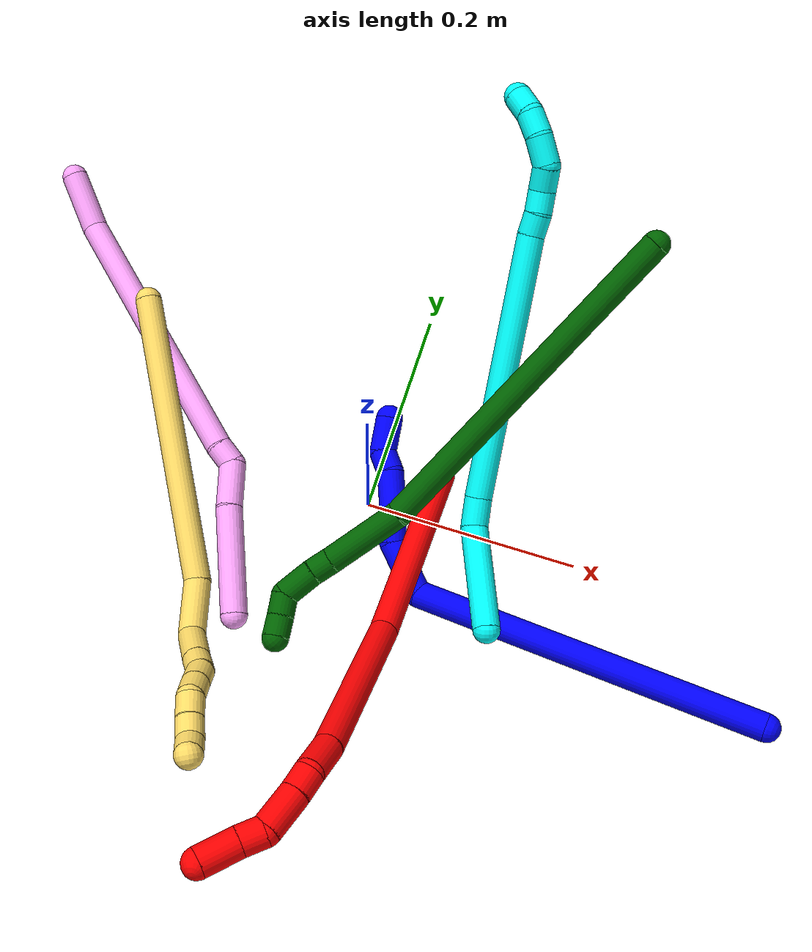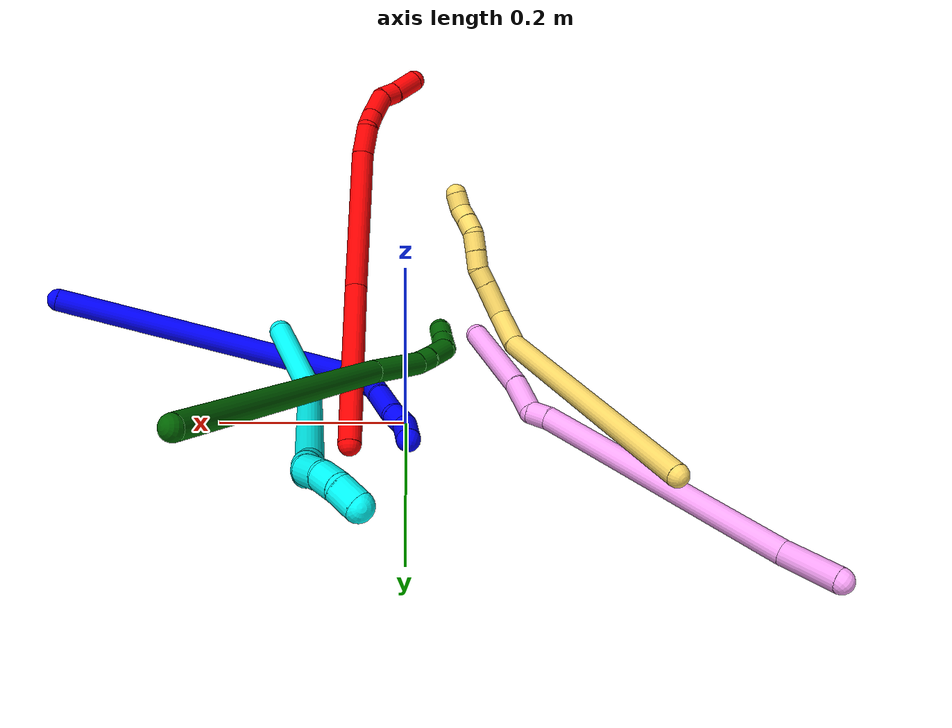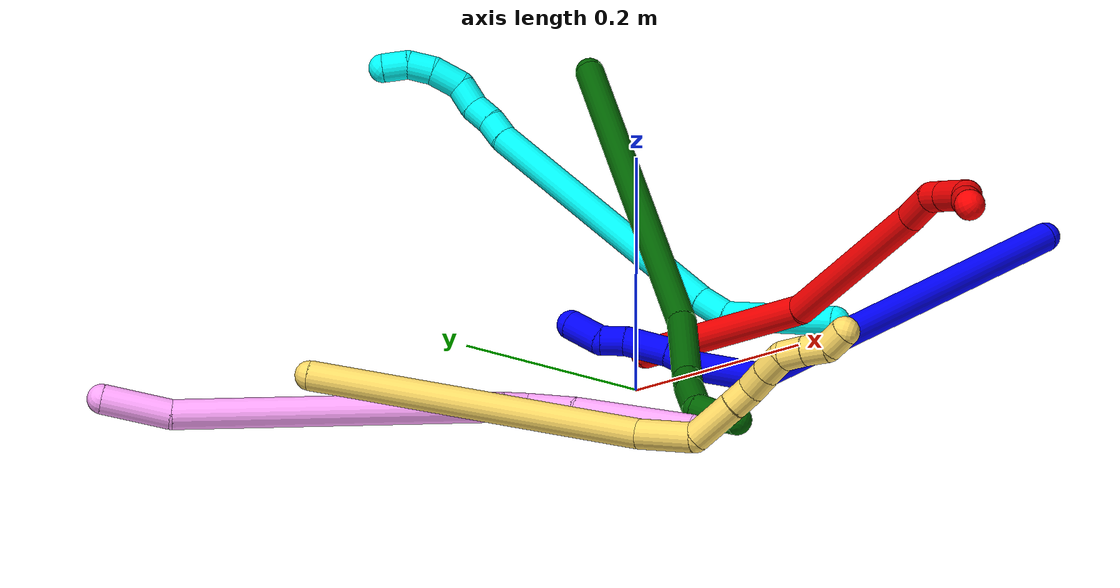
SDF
<sdf version="1.7">
 <world name="default">
  <plugin name="TubeGeneratorPlugin" filename="libtube_generator_plugin.so"/>
  <model name="photoneo_s_sensor">
   <static>1</static>
   <pose>0 0 2 1.57079 1.57079 3.14159</pose>
   <link name="link">
    <inertial><mass>0.1</mass></inertial>
    <sensor name="sensor" type="depth">
     <update_rate>30</update_rate>
     <camera>
      <horizontal_fov>1.22</horizontal_fov>
      <image><width>1920</width><height>1200</height><format>B8G8R8</format></image>
      <clip><near>0.1</near><far>4</far></clip>
      <depth_camera><output>points</output></depth_camera>
     </camera>
     <plugin name="camera_plugin" filename="libgazebo_ros_depth_camera.so">
      <baseline>0.2</baseline>
      <alwaysOn>1</alwaysOn>
      <updateRate>0.0</updateRate>
      <cameraName>camera_ir</cameraName>
      <imageTopicName>/camera/color/image_raw</imageTopicName>
      <cameraInfoTopicName>/camera/color/camera_info</cameraInfoTopicName>
      <depthImageTopicName>/camera/depth/image_raw</depthImageTopicName>
      <depthImageCameraInfoTopicName>/camera/depth/camera_info</depthImageCameraInfoTopicName>
      <pointCloudTopicName>/camera/depth/points</pointCloudTopicName>
      <frameName>fr_optical</frameName>
      <pointCloudCutoff>0.1</pointCloudCutoff>
      <pointCloudCutoffMax>2.0</pointCloudCutoffMax>
      <distortionK1>0</distortionK1>
      <distortionK2>0</distortionK2>
      <distortionK3>0</distortionK3>
      <distortionT1>0</distortionT1>
      <distortionT2>0</distortionT2>
      <CxPrime>0</CxPrime>
      <Cx>0</Cx>
      <Cy>0</Cy>
      <focalLength>0</focalLength>
      <hackBaseline>0</hackBaseline>
     </plugin>
    </sensor>
   </link>
  </model>
  <gravity>0 0 -9.8</gravity>
  <magnetic_field>6e-06 2.3e-05 -4.2e-05</magnetic_field>
  <atmosphere type="adiabatic"/>
  <physics name="default_physics" default="0" type="ode">
   <max_step_size>0.003</max_step_size>
   <real_time_factor>1</real_time_factor>
   <real_time_update_rate>1000</real_time_update_rate>
   <max_contacts>10000</max_contacts>
   <ode>
    <solver>
     <type>quick</type>
     <iters>100</iters>
     <sor>1.3</sor>
     <use_dynamic_moi_rescaling>0</use_dynamic_moi_rescaling>
    </solver>
    <constraints>
     <contact_max_correcting_vel>0</contact_max_correcting_vel>
     <contact_surface_layer>0.001</contact_surface_layer>
     <cfm>0</cfm>
     <erp>0.2</erp>
    </constraints>
   </ode>
  </physics>
  <scene><ambient>0.4 0.4 0.4 1</ambient><background>0.7 0.7 0.7 1</background><shadows>0</shadows></scene>
  <audio><device>default</device></audio>
  <spherical_coordinates>
   <surface_model>EARTH_WGS84</surface_model>
   <latitude_deg>0</latitude_deg>
   <longitude_deg>0</longitude_deg>
   <elevation>0</elevation>
   <heading_deg>0</heading_deg>
  </spherical_coordinates>
  <model name="bin">
   <static>1</static>
   <link name="bottom">
    <collision name="collision-bottom">
     <pose>0 0 -0.01 0 -0 0</pose>
     <geometry><box><size>0.8 0.6 0.02</size></box></geometry>
     <surface>
      <friction><ode><mu>100</mu><mu2>100</mu2></ode></friction>
      <contact><collide_bitmask>65535</collide_bitmask></contact>
     </surface>
    </collision>
   </link>
   <link name="west_wall">
    <collision name="collision-west_wall">
     <pose>-0.41 0 0.1 0 -0 0</pose>
     <geometry><box><size>0.02 0.6 0.2</size></box></geometry>
     <surface>
      <friction><ode><mu>100</mu><mu2>100</mu2></ode></friction>
      <contact><collide_bitmask>65535</collide_bitmask></contact>
     </surface>
    </collision>
   </link>
   <link name="east_wall">
    <collision name="collision-east_wall">
     <pose>0.41 0 0.1 0 -0 0</pose>
     <geometry><box><size>0.02 0.6 0.2</size></box></geometry>
     <surface>
      <friction><ode><mu>100</mu><mu2>100</mu2></ode></friction>
      <contact><collide_bitmask>65535</collide_bitmask></contact>
     </surface>
    </collision>
   </link>
   <link name="south_wall">
    <collision name="collision-south_wall">
     <pose>0 -0.31 0.1 0 -0 0</pose>
     <geometry><box><size>0.8 0.02 0.2</size></box></geometry>
     <surface>
      <friction><ode><mu>100</mu><mu2>100</mu2></ode></friction>
      <contact><collide_bitmask>65535</collide_bitmask></contact>
     </surface>
    </collision>
   </link>
   <link name="north_wall">
    <collision name="collision-north_wall">
     <pose>0 0.31 0.1 0 -0 0</pose>
     <geometry><box><size>0.8 0.02 0.2</size></box></geometry>
     <surface>
      <friction><ode><mu>100</mu><mu2>100</mu2></ode></friction>
      <contact><collide_bitmask>65535</collide_bitmask></contact>
     </surface>
    </collision>
   </link>
  </model>
  <model name="1">
   <static>0</static>
   <link name="1">
    <collision name="collision-cylinder-e_1_1_4">
     <pose>-0.016482 -0.009009 -0.163016 3.08638 -0.100614 -2.13835</pose>
     <geometry><cylinder><radius>0.0125</radius><length>0.32819</length></cylinder></geometry>
     <surface>
      <friction><ode><mu>1.16</mu><mu2>1.16</mu2><slip1>0</slip1><slip2>0</slip2></ode></friction>
      <contact><ode><kp>1e+06</kp><kd>1</kd><max_vel>0</max_vel><min_depth>0.001</min_depth></ode></contact>
     </surface>
    </collision>
    <visual name="visual-cylinder-e_1_1_4">
     <pose>-0.016482 -0.009009 -0.163016 3.08638 -0.100614 -2.13835</pose>
     <geometry><cylinder><radius>0.0125</radius><length>0.32819</length></cylinder></geometry>
     <material><ambient>0 0 1 1</ambient></material>
    </visual>
    <collision name="collision-cylinder-e_2_4_5">
     <pose>-0.042324 -0.002231 -0.344861 -2.44381 -0.363937 0.936588</pose>
     <geometry><cylinder><radius>0.0125</radius><length>0.052586</length></cylinder></geometry>
     <surface>
      <friction><ode><mu>1.16</mu><mu2>1.16</mu2><slip1>0</slip1><slip2>0</slip2></ode></friction>
      <contact><ode><kp>1e+06</kp><kd>1</kd><max_vel>0</max_vel><min_depth>0.001</min_depth></ode></contact>
     </surface>
    </collision>
    <visual name="visual-cylinder-e_2_4_5">
     <pose>-0.042324 -0.002231 -0.344861 -2.44381 -0.363937 0.936588</pose>
     <geometry><cylinder><radius>0.0125</radius><length>0.052586</length></cylinder></geometry>
     <material><ambient>0 0 1 1</ambient></material>
    </visual>
    <collision name="collision-cylinder-e_3_5_6">
     <pose>-0.056415 0.024815 -0.367709 -1.91379 -0.376904 0.528572</pose>
     <geometry><cylinder><radius>0.0125</radius><length>0.025715</length></cylinder></geometry>
     <surface>
      <friction><ode><mu>1.16</mu><mu2>1.16</mu2><slip1>0</slip1><slip2>0</slip2></ode></friction>
      <contact><ode><kp>1e+06</kp><kd>1</kd><max_vel>0</max_vel><min_depth>0.001</min_depth></ode></contact>
     </surface>
    </collision>
    <visual name="visual-cylinder-e_3_5_6">
     <pose>-0.056415 0.024815 -0.367709 -1.91379 -0.376904 0.528572</pose>
     <geometry><cylinder><radius>0.0125</radius><length>0.025715</length></cylinder></geometry>
     <material><ambient>0 0 1 1</ambient></material>
    </visual>
    <collision name="collision-cylinder-e_4_6_7">
     <pose>-0.065465 0.053141 -0.381028 -2.06966 -0.218614 0.365413</pose>
     <geometry><cylinder><radius>0.0125</radius><length>0.039819</length></cylinder></geometry>
     <surface>
      <friction><ode><mu>1.16</mu><mu2>1.16</mu2><slip1>0</slip1><slip2>0</slip2></ode></friction>
      <contact><ode><kp>1e+06</kp><kd>1</kd><max_vel>0</max_vel><min_depth>0.001</min_depth></ode></contact>
     </surface>
    </collision>
    <visual name="visual-cylinder-e_4_6_7">
     <pose>-0.065465 0.053141 -0.381028 -2.06966 -0.218614 0.365413</pose>
     <geometry><cylinder><radius>0.0125</radius><length>0.039819</length></cylinder></geometry>
     <material><ambient>0 0 1 1</ambient></material>
    </visual>
    <collision name="collision-cylinder-e_5_7_8">
     <pose>-0.071224 0.07743 -0.39789 -2.37927 -0.136872 0.338788</pose>
     <geometry><cylinder><radius>0.0125</radius><length>0.021112</length></cylinder></geometry>
     <surface>
      <friction><ode><mu>1.16</mu><mu2>1.16</mu2><slip1>0</slip1><slip2>0</slip2></ode></friction>
      <contact><ode><kp>1e+06</kp><kd>1</kd><max_vel>0</max_vel><min_depth>0.001</min_depth></ode></contact>
     </surface>
    </collision>
    <visual name="visual-cylinder-e_5_7_8">
     <pose>-0.071224 0.07743 -0.39789 -2.37927 -0.136872 0.338788</pose>
     <geometry><cylinder><radius>0.0125</radius><length>0.021112</length></cylinder></geometry>
     <material><ambient>0 0 1 1</ambient></material>
    </visual>
    <collision name="collision-cylinder-e_6_8_2">
     <pose>-0.076664 0.100091 -0.408761 -1.78182 -0.248112 0.306063</pose>
     <geometry><cylinder><radius>0.0125</radius><length>0.032577</length></cylinder></geometry>
     <surface>
      <friction><ode><mu>1.16</mu><mu2>1.16</mu2><slip1>0</slip1><slip2>0</slip2></ode></friction>
      <contact><ode><kp>1e+06</kp><kd>1</kd><max_vel>0</max_vel><min_depth>0.001</min_depth></ode></contact>
     </surface>
    </collision>
    <visual name="visual-cylinder-e_6_8_2">
     <pose>-0.076664 0.100091 -0.408761 -1.78182 -0.248112 0.306063</pose>
     <geometry><cylinder><radius>0.0125</radius><length>0.032577</length></cylinder></geometry>
     <material><ambient>0 0 1 1</ambient></material>
    </visual>
    <collision name="collision-sphere-2">
     <pose>-0.080664 0.115531 -0.412068 0 -0 0</pose>
     <geometry><sphere><radius>0.0125</radius></sphere></geometry>
     <surface>
      <friction><ode><mu>1.16</mu><mu2>1.16</mu2><slip1>0</slip1><slip2>0</slip2></ode></friction>
      <contact><ode><kp>1e+06</kp><kd>1</kd><max_vel>0</max_vel><min_depth>0.001</min_depth></ode></contact>
     </surface>
    </collision>
    <visual name="visual-sphere-2">
     <pose>-0.080664 0.115531 -0.412068 0 -0 0</pose>
     <geometry><sphere><radius>0.0125</radius></sphere></geometry>
     <material><ambient>0 0 1 1</ambient></material>
    </visual>
    <collision name="collision-sphere-4">
     <pose>-0.032965 -0.018019 -0.326033 0 -0 0</pose>
     <geometry><sphere><radius>0.0125</radius></sphere></geometry>
     <surface>
      <friction><ode><mu>1.16</mu><mu2>1.16</mu2><slip1>0</slip1><slip2>0</slip2></ode></friction>
      <contact><ode><kp>1e+06</kp><kd>1</kd><max_vel>0</max_vel><min_depth>0.001</min_depth></ode></contact>
     </surface>
    </collision>
    <visual name="visual-sphere-4">
     <pose>-0.032965 -0.018019 -0.326033 0 -0 0</pose>
     <geometry><sphere><radius>0.0125</radius></sphere></geometry>
     <material><ambient>0 0 1 1</ambient></material>
    </visual>
    <collision name="collision-sphere-1">
     <geometry><sphere><radius>0.0125</radius></sphere></geometry>
     <surface>
      <friction><ode><mu>1.16</mu><mu2>1.16</mu2><slip1>0</slip1><slip2>0</slip2></ode></friction>
      <contact><ode><kp>1e+06</kp><kd>1</kd><max_vel>0</max_vel><min_depth>0.001</min_depth></ode></contact>
     </surface>
    </collision>
    <visual name="visual-sphere-1">
     <geometry><sphere><radius>0.0125</radius></sphere></geometry>
     <material><ambient>0 0 1 1</ambient></material>
    </visual>
    <collision name="collision-sphere-8">
     <pose>-0.072664 0.084652 -0.405453 0 -0 0</pose>
     <geometry><sphere><radius>0.0125</radius></sphere></geometry>
     <surface>
      <friction><ode><mu>1.16</mu><mu2>1.16</mu2><slip1>0</slip1><slip2>0</slip2></ode></friction>
      <contact><ode><kp>1e+06</kp><kd>1</kd><max_vel>0</max_vel><min_depth>0.001</min_depth></ode></contact>
     </surface>
    </collision>
    <visual name="visual-sphere-8">
     <pose>-0.072664 0.084652 -0.405453 0 -0 0</pose>
     <geometry><sphere><radius>0.0125</radius></sphere></geometry>
     <material><ambient>0 0 1 1</ambient></material>
    </visual>
    <collision name="collision-sphere-5">
     <pose>-0.051683 0.013556 -0.363689 0 -0 0</pose>
     <geometry><sphere><radius>0.0125</radius></sphere></geometry>
     <surface>
      <friction><ode><mu>1.16</mu><mu2>1.16</mu2><slip1>0</slip1><slip2>0</slip2></ode></friction>
      <contact><ode><kp>1e+06</kp><kd>1</kd><max_vel>0</max_vel><min_depth>0.001</min_depth></ode></contact>
     </surface>
    </collision>
    <visual name="visual-sphere-5">
     <pose>-0.051683 0.013556 -0.363689 0 -0 0</pose>
     <geometry><sphere><radius>0.0125</radius></sphere></geometry>
     <material><ambient>0 0 1 1</ambient></material>
    </visual>
    <collision name="collision-sphere-6">
     <pose>-0.061147 0.036074 -0.37173 0 -0 0</pose>
     <geometry><sphere><radius>0.0125</radius></sphere></geometry>
     <surface>
      <friction><ode><mu>1.16</mu><mu2>1.16</mu2><slip1>0</slip1><slip2>0</slip2></ode></friction>
      <contact><ode><kp>1e+06</kp><kd>1</kd><max_vel>0</max_vel><min_depth>0.001</min_depth></ode></contact>
     </surface>
    </collision>
    <visual name="visual-sphere-6">
     <pose>-0.061147 0.036074 -0.37173 0 -0 0</pose>
     <geometry><sphere><radius>0.0125</radius></sphere></geometry>
     <material><ambient>0 0 1 1</ambient></material>
    </visual>
    <collision name="collision-sphere-7">
     <pose>-0.069783 0.070208 -0.390327 0 -0 0</pose>
     <geometry><sphere><radius>0.0125</radius></sphere></geometry>
     <surface>
      <friction><ode><mu>1.16</mu><mu2>1.16</mu2><slip1>0</slip1><slip2>0</slip2></ode></friction>
      <contact><ode><kp>1e+06</kp><kd>1</kd><max_vel>0</max_vel><min_depth>0.001</min_depth></ode></contact>
     </surface>
    </collision>
    <visual name="visual-sphere-7">
     <pose>-0.069783 0.070208 -0.390327 0 -0 0</pose>
     <geometry><sphere><radius>0.0125</radius></sphere></geometry>
     <material><ambient>0 0 1 1</ambient></material>
    </visual>
    <inertial>
     <pose>-0.031387 0.009151 -0.23596 0 -0 0</pose>
     <mass>0.5</mass>
     <inertia>
      <ixx>-0.004034</ixx>
      <ixy>0</ixy>
      <ixz>0</ixz>
      <iyy>-0.000864</iyy>
      <iyz>0</iyz>
      <izz>0.000415</izz>
     </inertia>
    </inertial>
   </link>
   <pose>0.388502 -0.114221 0.080601 0.302176 1.24822 0.120667</pose>
  </model>
  <model name="2">
   <static>0</static>
   <link name="2">
    <collision name="collision-cylinder-e_1_1_4">
     <pose>0.001164 -0.013631 0.095627 0.141585 0.012051 0.000855</pose>
     <geometry><cylinder><radius>0.0125</radius><length>0.193202</length></cylinder></geometry>
     <surface>
      <friction><ode><mu>1.16</mu><mu2>1.16</mu2><slip1>0</slip1><slip2>0</slip2></ode></friction>
      <contact><ode><kp>1e+06</kp><kd>1</kd><max_vel>0</max_vel><min_depth>0.001</min_depth></ode></contact>
     </surface>
    </collision>
    <visual name="visual-cylinder-e_1_1_4">
     <pose>0.001164 -0.013631 0.095627 0.141585 0.012051 0.000855</pose>
     <geometry><cylinder><radius>0.0125</radius><length>0.193202</length></cylinder></geometry>
     <material><ambient>1 0 0 1</ambient></material>
    </visual>
    <collision name="collision-cylinder-e_2_4_5">
     <pose>-0.005063 -0.015868 0.271302 -0.141382 -0.091165 0.00646</pose>
     <geometry><cylinder><radius>0.0125</radius><length>0.162382</length></cylinder></geometry>
     <surface>
      <friction><ode><mu>1.16</mu><mu2>1.16</mu2><slip1>0</slip1><slip2>0</slip2></ode></friction>
      <contact><ode><kp>1e+06</kp><kd>1</kd><max_vel>0</max_vel><min_depth>0.001</min_depth></ode></contact>
     </surface>
    </collision>
    <visual name="visual-cylinder-e_2_4_5">
     <pose>-0.005063 -0.015868 0.271302 -0.141382 -0.091165 0.00646</pose>
     <geometry><cylinder><radius>0.0125</radius><length>0.162382</length></cylinder></geometry>
     <material><ambient>1 0 0 1</ambient></material>
    </visual>
    <collision name="collision-cylinder-e_3_5_6">
     <pose>-0.016153 -0.002178 0.36784 -0.138373 -0.218532 0.015204</pose>
     <geometry><cylinder><radius>0.0125</radius><length>0.034112</length></cylinder></geometry>
     <surface>
      <friction><ode><mu>1.16</mu><mu2>1.16</mu2><slip1>0</slip1><slip2>0</slip2></ode></friction>
      <contact><ode><kp>1e+06</kp><kd>1</kd><max_vel>0</max_vel><min_depth>0.001</min_depth></ode></contact>
     </surface>
    </collision>
    <visual name="visual-cylinder-e_3_5_6">
     <pose>-0.016153 -0.002178 0.36784 -0.138373 -0.218532 0.015204</pose>
     <geometry><cylinder><radius>0.0125</radius><length>0.034112</length></cylinder></geometry>
     <material><ambient>1 0 0 1</ambient></material>
    </visual>
    <collision name="collision-cylinder-e_4_6_7">
     <pose>-0.021638 -0.003044 0.393792 0.322634 -0.177331 -0.028931</pose>
     <geometry><cylinder><radius>0.0125</radius><length>0.020269</length></cylinder></geometry>
     <surface>
      <friction><ode><mu>1.16</mu><mu2>1.16</mu2><slip1>0</slip1><slip2>0</slip2></ode></friction>
      <contact><ode><kp>1e+06</kp><kd>1</kd><max_vel>0</max_vel><min_depth>0.001</min_depth></ode></contact>
     </surface>
    </collision>
    <visual name="visual-cylinder-e_4_6_7">
     <pose>-0.021638 -0.003044 0.393792 0.322634 -0.177331 -0.028931</pose>
     <geometry><cylinder><radius>0.0125</radius><length>0.020269</length></cylinder></geometry>
     <material><ambient>1 0 0 1</ambient></material>
    </visual>
    <collision name="collision-cylinder-e_5_7_8">
     <pose>-0.027846 -0.012052 0.419649 0.342431 -0.248691 -0.043217</pose>
     <geometry><cylinder><radius>0.0125</radius><length>0.035919</length></cylinder></geometry>
     <surface>
      <friction><ode><mu>1.16</mu><mu2>1.16</mu2><slip1>0</slip1><slip2>0</slip2></ode></friction>
      <contact><ode><kp>1e+06</kp><kd>1</kd><max_vel>0</max_vel><min_depth>0.001</min_depth></ode></contact>
     </surface>
    </collision>
    <visual name="visual-cylinder-e_5_7_8">
     <pose>-0.027846 -0.012052 0.419649 0.342431 -0.248691 -0.043217</pose>
     <geometry><cylinder><radius>0.0125</radius><length>0.035919</length></cylinder></geometry>
     <material><ambient>1 0 0 1</ambient></material>
    </visual>
    <collision name="collision-cylinder-e_6_8_9">
     <pose>-0.039163 -0.022944 0.441758 0.723612 -0.735417 -0.289553</pose>
     <geometry><cylinder><radius>0.0125</radius><length>0.020559</length></cylinder></geometry>
     <surface>
      <friction><ode><mu>1.16</mu><mu2>1.16</mu2><slip1>0</slip1><slip2>0</slip2></ode></friction>
      <contact><ode><kp>1e+06</kp><kd>1</kd><max_vel>0</max_vel><min_depth>0.001</min_depth></ode></contact>
     </surface>
    </collision>
    <visual name="visual-cylinder-e_6_8_9">
     <pose>-0.039163 -0.022944 0.441758 0.723612 -0.735417 -0.289553</pose>
     <geometry><cylinder><radius>0.0125</radius><length>0.020559</length></cylinder></geometry>
     <material><ambient>1 0 0 1</ambient></material>
    </visual>
    <collision name="collision-cylinder-e_7_9_2">
     <pose>-0.056476 -0.034671 0.458802 0.532642 -0.669793 -0.189305</pose>
     <geometry><cylinder><radius>0.0125</radius><length>0.033557</length></cylinder></geometry>
     <surface>
      <friction><ode><mu>1.16</mu><mu2>1.16</mu2><slip1>0</slip1><slip2>0</slip2></ode></friction>
      <contact><ode><kp>1e+06</kp><kd>1</kd><max_vel>0</max_vel><min_depth>0.001</min_depth></ode></contact>
     </surface>
    </collision>
    <visual name="visual-cylinder-e_7_9_2">
     <pose>-0.056476 -0.034671 0.458802 0.532642 -0.669793 -0.189305</pose>
     <geometry><cylinder><radius>0.0125</radius><length>0.033557</length></cylinder></geometry>
     <material><ambient>1 0 0 1</ambient></material>
    </visual>
    <collision name="collision-sphere-2">
     <pose>-0.066893 -0.04135 0.470134 0 -0 0</pose>
     <geometry><sphere><radius>0.0125</radius></sphere></geometry>
     <surface>
      <friction><ode><mu>1.16</mu><mu2>1.16</mu2><slip1>0</slip1><slip2>0</slip2></ode></friction>
      <contact><ode><kp>1e+06</kp><kd>1</kd><max_vel>0</max_vel><min_depth>0.001</min_depth></ode></contact>
     </surface>
    </collision>
    <visual name="visual-sphere-2">
     <pose>-0.066893 -0.04135 0.470134 0 -0 0</pose>
     <geometry><sphere><radius>0.0125</radius></sphere></geometry>
     <material><ambient>1 0 0 1</ambient></material>
    </visual>
    <collision name="collision-sphere-9">
     <pose>-0.046059 -0.027991 0.447471 0 -0 0</pose>
     <geometry><sphere><radius>0.0125</radius></sphere></geometry>
     <surface>
      <friction><ode><mu>1.16</mu><mu2>1.16</mu2><slip1>0</slip1><slip2>0</slip2></ode></friction>
      <contact><ode><kp>1e+06</kp><kd>1</kd><max_vel>0</max_vel><min_depth>0.001</min_depth></ode></contact>
     </surface>
    </collision>
    <visual name="visual-sphere-9">
     <pose>-0.046059 -0.027991 0.447471 0 -0 0</pose>
     <geometry><sphere><radius>0.0125</radius></sphere></geometry>
     <material><ambient>1 0 0 1</ambient></material>
    </visual>
    <collision name="collision-sphere-4">
     <pose>0.002328 -0.027261 0.191255 0 -0 0</pose>
     <geometry><sphere><radius>0.0125</radius></sphere></geometry>
     <surface>
      <friction><ode><mu>1.16</mu><mu2>1.16</mu2><slip1>0</slip1><slip2>0</slip2></ode></friction>
      <contact><ode><kp>1e+06</kp><kd>1</kd><max_vel>0</max_vel><min_depth>0.001</min_depth></ode></contact>
     </surface>
    </collision>
    <visual name="visual-sphere-4">
     <pose>0.002328 -0.027261 0.191255 0 -0 0</pose>
     <geometry><sphere><radius>0.0125</radius></sphere></geometry>
     <material><ambient>1 0 0 1</ambient></material>
    </visual>
    <collision name="collision-sphere-1">
     <geometry><sphere><radius>0.0125</radius></sphere></geometry>
     <surface>
      <friction><ode><mu>1.16</mu><mu2>1.16</mu2><slip1>0</slip1><slip2>0</slip2></ode></friction>
      <contact><ode><kp>1e+06</kp><kd>1</kd><max_vel>0</max_vel><min_depth>0.001</min_depth></ode></contact>
     </surface>
    </collision>
    <visual name="visual-sphere-1">
     <geometry><sphere><radius>0.0125</radius></sphere></geometry>
     <material><ambient>1 0 0 1</ambient></material>
    </visual>
    <collision name="collision-sphere-8">
     <pose>-0.032267 -0.017897 0.436046 0 -0 0</pose>
     <geometry><sphere><radius>0.0125</radius></sphere></geometry>
     <surface>
      <friction><ode><mu>1.16</mu><mu2>1.16</mu2><slip1>0</slip1><slip2>0</slip2></ode></friction>
      <contact><ode><kp>1e+06</kp><kd>1</kd><max_vel>0</max_vel><min_depth>0.001</min_depth></ode></contact>
     </surface>
    </collision>
    <visual name="visual-sphere-8">
     <pose>-0.032267 -0.017897 0.436046 0 -0 0</pose>
     <geometry><sphere><radius>0.0125</radius></sphere></geometry>
     <material><ambient>1 0 0 1</ambient></material>
    </visual>
    <collision name="collision-sphere-5">
     <pose>-0.012455 -0.004475 0.351349 0 -0 0</pose>
     <geometry><sphere><radius>0.0125</radius></sphere></geometry>
     <surface>
      <friction><ode><mu>1.16</mu><mu2>1.16</mu2><slip1>0</slip1><slip2>0</slip2></ode></friction>
      <contact><ode><kp>1e+06</kp><kd>1</kd><max_vel>0</max_vel><min_depth>0.001</min_depth></ode></contact>
     </surface>
    </collision>
    <visual name="visual-sphere-5">
     <pose>-0.012455 -0.004475 0.351349 0 -0 0</pose>
     <geometry><sphere><radius>0.0125</radius></sphere></geometry>
     <material><ambient>1 0 0 1</ambient></material>
    </visual>
    <collision name="collision-sphere-6">
     <pose>-0.01985 0.000118 0.384331 0 -0 0</pose>
     <geometry><sphere><radius>0.0125</radius></sphere></geometry>
     <surface>
      <friction><ode><mu>1.16</mu><mu2>1.16</mu2><slip1>0</slip1><slip2>0</slip2></ode></friction>
      <contact><ode><kp>1e+06</kp><kd>1</kd><max_vel>0</max_vel><min_depth>0.001</min_depth></ode></contact>
     </surface>
    </collision>
    <visual name="visual-sphere-6">
     <pose>-0.01985 0.000118 0.384331 0 -0 0</pose>
     <geometry><sphere><radius>0.0125</radius></sphere></geometry>
     <material><ambient>1 0 0 1</ambient></material>
    </visual>
    <collision name="collision-sphere-7">
     <pose>-0.023426 -0.006207 0.403253 0 -0 0</pose>
     <geometry><sphere><radius>0.0125</radius></sphere></geometry>
     <surface>
      <friction><ode><mu>1.16</mu><mu2>1.16</mu2><slip1>0</slip1><slip2>0</slip2></ode></friction>
      <contact><ode><kp>1e+06</kp><kd>1</kd><max_vel>0</max_vel><min_depth>0.001</min_depth></ode></contact>
     </surface>
    </collision>
    <visual name="visual-sphere-7">
     <pose>-0.023426 -0.006207 0.403253 0 -0 0</pose>
     <geometry><sphere><radius>0.0125</radius></sphere></geometry>
     <material><ambient>1 0 0 1</ambient></material>
    </visual>
    <inertial>
     <pose>-0.010575 -0.014828 0.245222 0 -0 0</pose>
     <mass>0.5</mass>
     <inertia>
      <ixx>0.000982</ixx>
      <ixy>0</ixy>
      <ixz>0</ixz>
      <iyy>0.000977</iyy>
      <iyz>0</iyz>
      <izz>0.000108</izz>
     </inertia>
    </inertial>
   </link>
   <pose>0.05799 0.045137 0.011497 1.03028 0.234329 -0.117136</pose>
  </model>
  <model name="3">
   <static>0</static>
   <link name="3">
    <collision name="collision-cylinder-e_1_1_4">
     <pose>-0.018673 0.025532 0.036896 -0.605334 -0.394379 0.124609</pose>
     <geometry><cylinder><radius>0.0125</radius><length>0.097198</length></cylinder></geometry>
     <surface>
      <friction><ode><mu>1.16</mu><mu2>1.16</mu2><slip1>0</slip1><slip2>0</slip2></ode></friction>
      <contact><ode><kp>1e+06</kp><kd>1</kd><max_vel>0</max_vel><min_depth>0.001</min_depth></ode></contact>
     </surface>
    </collision>
    <visual name="visual-cylinder-e_1_1_4">
     <pose>-0.018673 0.025532 0.036896 -0.605334 -0.394379 0.124609</pose>
     <geometry><cylinder><radius>0.0125</radius><length>0.097198</length></cylinder></geometry>
     <material><ambient>0.003922 1 0.996078 1</ambient></material>
    </visual>
    <collision name="collision-cylinder-e_2_4_5">
     <pose>-0.037482 0.055346 0.086834 -0.317299 -0.009873 0.00158</pose>
     <geometry><cylinder><radius>0.0125</radius><length>0.027456</length></cylinder></geometry>
     <surface>
      <friction><ode><mu>1.16</mu><mu2>1.16</mu2><slip1>0</slip1><slip2>0</slip2></ode></friction>
      <contact><ode><kp>1e+06</kp><kd>1</kd><max_vel>0</max_vel><min_depth>0.001</min_depth></ode></contact>
     </surface>
    </collision>
    <visual name="visual-cylinder-e_2_4_5">
     <pose>-0.037482 0.055346 0.086834 -0.317299 -0.009873 0.00158</pose>
     <geometry><cylinder><radius>0.0125</radius><length>0.027456</length></cylinder></geometry>
     <material><ambient>0.003922 1 0.996078 1</ambient></material>
    </visual>
    <collision name="collision-cylinder-e_3_5_6">
     <pose>-0.027229 0.089054 0.216009 -0.248151 0.086503 -0.010795</pose>
     <geometry><cylinder><radius>0.0125</radius><length>0.240506</length></cylinder></geometry>
     <surface>
      <friction><ode><mu>1.16</mu><mu2>1.16</mu2><slip1>0</slip1><slip2>0</slip2></ode></friction>
      <contact><ode><kp>1e+06</kp><kd>1</kd><max_vel>0</max_vel><min_depth>0.001</min_depth></ode></contact>
     </surface>
    </collision>
    <visual name="visual-cylinder-e_3_5_6">
     <pose>-0.027229 0.089054 0.216009 -0.248151 0.086503 -0.010795</pose>
     <geometry><cylinder><radius>0.0125</radius><length>0.240506</length></cylinder></geometry>
     <material><ambient>0.003922 1 0.996078 1</ambient></material>
    </visual>
    <collision name="collision-cylinder-e_4_6_7">
     <pose>-0.014141 0.119645 0.341942 -0.11833 0.266888 -0.015903</pose>
     <geometry><cylinder><radius>0.0125</radius><length>0.020462</length></cylinder></geometry>
     <surface>
      <friction><ode><mu>1.16</mu><mu2>1.16</mu2><slip1>0</slip1><slip2>0</slip2></ode></friction>
      <contact><ode><kp>1e+06</kp><kd>1</kd><max_vel>0</max_vel><min_depth>0.001</min_depth></ode></contact>
     </surface>
    </collision>
    <visual name="visual-cylinder-e_4_6_7">
     <pose>-0.014141 0.119645 0.341942 -0.11833 0.266888 -0.015903</pose>
     <geometry><cylinder><radius>0.0125</radius><length>0.020462</length></cylinder></geometry>
     <material><ambient>0.003922 1 0.996078 1</ambient></material>
    </visual>
    <collision name="collision-cylinder-e_5_7_8">
     <pose>-0.010624 0.123017 0.361827 -0.215466 0.079143 -0.008564</pose>
     <geometry><cylinder><radius>0.0125</radius><length>0.020714</length></cylinder></geometry>
     <surface>
      <friction><ode><mu>1.16</mu><mu2>1.16</mu2><slip1>0</slip1><slip2>0</slip2></ode></friction>
      <contact><ode><kp>1e+06</kp><kd>1</kd><max_vel>0</max_vel><min_depth>0.001</min_depth></ode></contact>
     </surface>
    </collision>
    <visual name="visual-cylinder-e_5_7_8">
     <pose>-0.010624 0.123017 0.361827 -0.215466 0.079143 -0.008564</pose>
     <geometry><cylinder><radius>0.0125</radius><length>0.020714</length></cylinder></geometry>
     <material><ambient>0.003922 1 0.996078 1</ambient></material>
    </visual>
    <collision name="collision-cylinder-e_6_8_9">
     <pose>-0.007343 0.123898 0.382914 0.12 0.218635 0.013186</pose>
     <geometry><cylinder><radius>0.0125</radius><length>0.022702</length></cylinder></geometry>
     <surface>
      <friction><ode><mu>1.16</mu><mu2>1.16</mu2><slip1>0</slip1><slip2>0</slip2></ode></friction>
      <contact><ode><kp>1e+06</kp><kd>1</kd><max_vel>0</max_vel><min_depth>0.001</min_depth></ode></contact>
     </surface>
    </collision>
    <visual name="visual-cylinder-e_6_8_9">
     <pose>-0.007343 0.123898 0.382914 0.12 0.218635 0.013186</pose>
     <geometry><cylinder><radius>0.0125</radius><length>0.022702</length></cylinder></geometry>
     <material><ambient>0.003922 1 0.996078 1</ambient></material>
    </visual>
    <collision name="collision-cylinder-e_7_9_10">
     <pose>-0.008954 0.122524 0.406663 0.003724 -0.309225 -0.00058</pose>
     <geometry><cylinder><radius>0.0125</radius><length>0.026765</length></cylinder></geometry>
     <surface>
      <friction><ode><mu>1.16</mu><mu2>1.16</mu2><slip1>0</slip1><slip2>0</slip2></ode></friction>
      <contact><ode><kp>1e+06</kp><kd>1</kd><max_vel>0</max_vel><min_depth>0.001</min_depth></ode></contact>
     </surface>
    </collision>
    <visual name="visual-cylinder-e_7_9_10">
     <pose>-0.008954 0.122524 0.406663 0.003724 -0.309225 -0.00058</pose>
     <geometry><cylinder><radius>0.0125</radius><length>0.026765</length></cylinder></geometry>
     <material><ambient>0.003922 1 0.996078 1</ambient></material>
    </visual>
    <collision name="collision-cylinder-e_8_10_11">
     <pose>-0.018312 0.124397 0.428966 -0.198352 -0.496925 0.050478</pose>
     <geometry><cylinder><radius>0.0125</radius><length>0.022174</length></cylinder></geometry>
     <surface>
      <friction><ode><mu>1.16</mu><mu2>1.16</mu2><slip1>0</slip1><slip2>0</slip2></ode></friction>
      <contact><ode><kp>1e+06</kp><kd>1</kd><max_vel>0</max_vel><min_depth>0.001</min_depth></ode></contact>
     </surface>
    </collision>
    <visual name="visual-cylinder-e_8_10_11">
     <pose>-0.018312 0.124397 0.428966 -0.198352 -0.496925 0.050478</pose>
     <geometry><cylinder><radius>0.0125</radius><length>0.022174</length></cylinder></geometry>
     <material><ambient>0.003922 1 0.996078 1</ambient></material>
    </visual>
    <collision name="collision-cylinder-e_9_11_2">
     <pose>-0.031258 0.13021 0.445407 -0.514493 -0.769415 0.212228</pose>
     <geometry><cylinder><radius>0.0125</radius><length>0.022023</length></cylinder></geometry>
     <surface>
      <friction><ode><mu>1.16</mu><mu2>1.16</mu2><slip1>0</slip1><slip2>0</slip2></ode></friction>
      <contact><ode><kp>1e+06</kp><kd>1</kd><max_vel>0</max_vel><min_depth>0.001</min_depth></ode></contact>
     </surface>
    </collision>
    <visual name="visual-cylinder-e_9_11_2">
     <pose>-0.031258 0.13021 0.445407 -0.514493 -0.769415 0.212228</pose>
     <geometry><cylinder><radius>0.0125</radius><length>0.022023</length></cylinder></geometry>
     <material><ambient>0.003922 1 0.996078 1</ambient></material>
    </visual>
    <collision name="collision-sphere-2">
     <pose>-0.038919 0.134102 0.452293 0 -0 0</pose>
     <geometry><sphere><radius>0.0125</radius></sphere></geometry>
     <surface>
      <friction><ode><mu>1.16</mu><mu2>1.16</mu2><slip1>0</slip1><slip2>0</slip2></ode></friction>
      <contact><ode><kp>1e+06</kp><kd>1</kd><max_vel>0</max_vel><min_depth>0.001</min_depth></ode></contact>
     </surface>
    </collision>
    <visual name="visual-sphere-2">
     <pose>-0.038919 0.134102 0.452293 0 -0 0</pose>
     <geometry><sphere><radius>0.0125</radius></sphere></geometry>
     <material><ambient>0.003922 1 0.996078 1</ambient></material>
    </visual>
    <collision name="collision-sphere-11">
     <pose>-0.023598 0.126317 0.438521 0 -0 0</pose>
     <geometry><sphere><radius>0.0125</radius></sphere></geometry>
     <surface>
      <friction><ode><mu>1.16</mu><mu2>1.16</mu2><slip1>0</slip1><slip2>0</slip2></ode></friction>
      <contact><ode><kp>1e+06</kp><kd>1</kd><max_vel>0</max_vel><min_depth>0.001</min_depth></ode></contact>
     </surface>
    </collision>
    <visual name="visual-sphere-11">
     <pose>-0.023598 0.126317 0.438521 0 -0 0</pose>
     <geometry><sphere><radius>0.0125</radius></sphere></geometry>
     <material><ambient>0.003922 1 0.996078 1</ambient></material>
    </visual>
    <collision name="collision-sphere-10">
     <pose>-0.013026 0.122476 0.419411 0 -0 0</pose>
     <geometry><sphere><radius>0.0125</radius></sphere></geometry>
     <surface>
      <friction><ode><mu>1.16</mu><mu2>1.16</mu2><slip1>0</slip1><slip2>0</slip2></ode></friction>
      <contact><ode><kp>1e+06</kp><kd>1</kd><max_vel>0</max_vel><min_depth>0.001</min_depth></ode></contact>
     </surface>
    </collision>
    <visual name="visual-sphere-10">
     <pose>-0.013026 0.122476 0.419411 0 -0 0</pose>
     <geometry><sphere><radius>0.0125</radius></sphere></geometry>
     <material><ambient>0.003922 1 0.996078 1</ambient></material>
    </visual>
    <collision name="collision-sphere-9">
     <pose>-0.004881 0.122571 0.393916 0 -0 0</pose>
     <geometry><sphere><radius>0.0125</radius></sphere></geometry>
     <surface>
      <friction><ode><mu>1.16</mu><mu2>1.16</mu2><slip1>0</slip1><slip2>0</slip2></ode></friction>
      <contact><ode><kp>1e+06</kp><kd>1</kd><max_vel>0</max_vel><min_depth>0.001</min_depth></ode></contact>
     </surface>
    </collision>
    <visual name="visual-sphere-9">
     <pose>-0.004881 0.122571 0.393916 0 -0 0</pose>
     <geometry><sphere><radius>0.0125</radius></sphere></geometry>
     <material><ambient>0.003922 1 0.996078 1</ambient></material>
    </visual>
    <collision name="collision-sphere-4">
     <pose>-0.037347 0.051064 0.073792 0 -0 0</pose>
     <geometry><sphere><radius>0.0125</radius></sphere></geometry>
     <surface>
      <friction><ode><mu>1.16</mu><mu2>1.16</mu2><slip1>0</slip1><slip2>0</slip2></ode></friction>
      <contact><ode><kp>1e+06</kp><kd>1</kd><max_vel>0</max_vel><min_depth>0.001</min_depth></ode></contact>
     </surface>
    </collision>
    <visual name="visual-sphere-4">
     <pose>-0.037347 0.051064 0.073792 0 -0 0</pose>
     <geometry><sphere><radius>0.0125</radius></sphere></geometry>
     <material><ambient>0.003922 1 0.996078 1</ambient></material>
    </visual>
    <collision name="collision-sphere-1">
     <geometry><sphere><radius>0.0125</radius></sphere></geometry>
     <surface>
      <friction><ode><mu>1.16</mu><mu2>1.16</mu2><slip1>0</slip1><slip2>0</slip2></ode></friction>
      <contact><ode><kp>1e+06</kp><kd>1</kd><max_vel>0</max_vel><min_depth>0.001</min_depth></ode></contact>
     </surface>
    </collision>
    <visual name="visual-sphere-1">
     <geometry><sphere><radius>0.0125</radius></sphere></geometry>
     <material><ambient>0.003922 1 0.996078 1</ambient></material>
    </visual>
    <collision name="collision-sphere-8">
     <pose>-0.009805 0.125224 0.371913 0 -0 0</pose>
     <geometry><sphere><radius>0.0125</radius></sphere></geometry>
     <surface>
      <friction><ode><mu>1.16</mu><mu2>1.16</mu2><slip1>0</slip1><slip2>0</slip2></ode></friction>
      <contact><ode><kp>1e+06</kp><kd>1</kd><max_vel>0</max_vel><min_depth>0.001</min_depth></ode></contact>
     </surface>
    </collision>
    <visual name="visual-sphere-8">
     <pose>-0.009805 0.125224 0.371913 0 -0 0</pose>
     <geometry><sphere><radius>0.0125</radius></sphere></geometry>
     <material><ambient>0.003922 1 0.996078 1</ambient></material>
    </visual>
    <collision name="collision-sphere-5">
     <pose>-0.037618 0.059629 0.099876 0 -0 0</pose>
     <geometry><sphere><radius>0.0125</radius></sphere></geometry>
     <surface>
      <friction><ode><mu>1.16</mu><mu2>1.16</mu2><slip1>0</slip1><slip2>0</slip2></ode></friction>
      <contact><ode><kp>1e+06</kp><kd>1</kd><max_vel>0</max_vel><min_depth>0.001</min_depth></ode></contact>
     </surface>
    </collision>
    <visual name="visual-sphere-5">
     <pose>-0.037618 0.059629 0.099876 0 -0 0</pose>
     <geometry><sphere><radius>0.0125</radius></sphere></geometry>
     <material><ambient>0.003922 1 0.996078 1</ambient></material>
    </visual>
    <collision name="collision-sphere-6">
     <pose>-0.016839 0.11848 0.332142 0 -0 0</pose>
     <geometry><sphere><radius>0.0125</radius></sphere></geometry>
     <surface>
      <friction><ode><mu>1.16</mu><mu2>1.16</mu2><slip1>0</slip1><slip2>0</slip2></ode></friction>
      <contact><ode><kp>1e+06</kp><kd>1</kd><max_vel>0</max_vel><min_depth>0.001</min_depth></ode></contact>
     </surface>
    </collision>
    <visual name="visual-sphere-6">
     <pose>-0.016839 0.11848 0.332142 0 -0 0</pose>
     <geometry><sphere><radius>0.0125</radius></sphere></geometry>
     <material><ambient>0.003922 1 0.996078 1</ambient></material>
    </visual>
    <collision name="collision-sphere-7">
     <pose>-0.011443 0.12081 0.351742 0 -0 0</pose>
     <geometry><sphere><radius>0.0125</radius></sphere></geometry>
     <surface>
      <friction><ode><mu>1.16</mu><mu2>1.16</mu2><slip1>0</slip1><slip2>0</slip2></ode></friction>
      <contact><ode><kp>1e+06</kp><kd>1</kd><max_vel>0</max_vel><min_depth>0.001</min_depth></ode></contact>
     </surface>
    </collision>
    <visual name="visual-sphere-7">
     <pose>-0.011443 0.12081 0.351742 0 -0 0</pose>
     <geometry><sphere><radius>0.0125</radius></sphere></geometry>
     <material><ambient>0.003922 1 0.996078 1</ambient></material>
    </visual>
    <inertial>
     <pose>-0.022806 0.084268 0.222624 0 -0 0</pose>
     <mass>0.5</mass>
     <inertia>
      <ixx>0.001245</ixx>
      <ixy>0</ixy>
      <ixz>0</ixz>
      <iyy>0.001222</iyy>
      <iyz>0</iyz>
      <izz>-0.000363</izz>
     </inertia>
    </inertial>
   </link>
   <pose>0.140275 -0.096295 0.050796 -0.853214 -0.403918 -0.012692</pose>
  </model>
  <model name="4">
   <static>0</static>
   <link name="4">
    <collision name="collision-cylinder-e_1_1_4">
     <pose>0.015112 -0.024898 -0.003543 1.71214 0.541083 0.618678</pose>
     <geometry><cylinder><radius>0.0125</radius><length>0.058679</length></cylinder></geometry>
     <surface>
      <friction><ode><mu>1.16</mu><mu2>1.16</mu2><slip1>0</slip1><slip2>0</slip2></ode></friction>
      <contact><ode><kp>1e+06</kp><kd>1</kd><max_vel>0</max_vel><min_depth>0.001</min_depth></ode></contact>
     </surface>
    </collision>
    <visual name="visual-cylinder-e_1_1_4">
     <pose>0.015112 -0.024898 -0.003543 1.71214 0.541083 0.618678</pose>
     <geometry><cylinder><radius>0.0125</radius><length>0.058679</length></cylinder></geometry>
     <material><ambient>1 0.65098 0.996078 1</ambient></material>
    </visual>
    <collision name="collision-cylinder-e_2_4_5">
     <pose>0.126508 -0.144561 -0.021362 1.72033 0.787738 0.899723</pose>
     <geometry><cylinder><radius>0.0125</radius><length>0.271699</length></cylinder></geometry>
     <surface>
      <friction><ode><mu>1.16</mu><mu2>1.16</mu2><slip1>0</slip1><slip2>0</slip2></ode></friction>
      <contact><ode><kp>1e+06</kp><kd>1</kd><max_vel>0</max_vel><min_depth>0.001</min_depth></ode></contact>
     </surface>
    </collision>
    <visual name="visual-cylinder-e_2_4_5">
     <pose>0.126508 -0.144561 -0.021362 1.72033 0.787738 0.899723</pose>
     <geometry><cylinder><radius>0.0125</radius><length>0.271699</length></cylinder></geometry>
     <material><ambient>1 0.65098 0.996078 1</ambient></material>
    </visual>
    <collision name="collision-cylinder-e_3_5_6">
     <pose>0.230168 -0.246869 -0.03873 1.95972 0.735476 1.04253</pose>
     <geometry><cylinder><radius>0.0125</radius><length>0.021986</length></cylinder></geometry>
     <surface>
      <friction><ode><mu>1.16</mu><mu2>1.16</mu2><slip1>0</slip1><slip2>0</slip2></ode></friction>
      <contact><ode><kp>1e+06</kp><kd>1</kd><max_vel>0</max_vel><min_depth>0.001</min_depth></ode></contact>
     </surface>
    </collision>
    <visual name="visual-cylinder-e_3_5_6">
     <pose>0.230168 -0.246869 -0.03873 1.95972 0.735476 1.04253</pose>
     <geometry><cylinder><radius>0.0125</radius><length>0.021986</length></cylinder></geometry>
     <material><ambient>1 0.65098 0.996078 1</ambient></material>
    </visual>
    <collision name="collision-cylinder-e_4_6_7">
     <pose>0.248263 -0.272233 -0.033408 1.12974 0.498184 0.319674</pose>
     <geometry><cylinder><radius>0.0125</radius><length>0.044869</length></cylinder></geometry>
     <surface>
      <friction><ode><mu>1.16</mu><mu2>1.16</mu2><slip1>0</slip1><slip2>0</slip2></ode></friction>
      <contact><ode><kp>1e+06</kp><kd>1</kd><max_vel>0</max_vel><min_depth>0.001</min_depth></ode></contact>
     </surface>
    </collision>
    <visual name="visual-cylinder-e_4_6_7">
     <pose>0.248263 -0.272233 -0.033408 1.12974 0.498184 0.319674</pose>
     <geometry><cylinder><radius>0.0125</radius><length>0.044869</length></cylinder></geometry>
     <material><ambient>1 0.65098 0.996078 1</ambient></material>
    </visual>
    <collision name="collision-cylinder-e_5_7_2">
     <pose>0.283729 -0.333366 -0.012666 1.29347 0.502474 0.382843</pose>
     <geometry><cylinder><radius>0.0125</radius><length>0.102768</length></cylinder></geometry>
     <surface>
      <friction><ode><mu>1.16</mu><mu2>1.16</mu2><slip1>0</slip1><slip2>0</slip2></ode></friction>
      <contact><ode><kp>1e+06</kp><kd>1</kd><max_vel>0</max_vel><min_depth>0.001</min_depth></ode></contact>
     </surface>
    </collision>
    <visual name="visual-cylinder-e_5_7_2">
     <pose>0.283729 -0.333366 -0.012666 1.29347 0.502474 0.382843</pose>
     <geometry><cylinder><radius>0.0125</radius><length>0.102768</length></cylinder></geometry>
     <material><ambient>1 0.65098 0.996078 1</ambient></material>
    </visual>
    <collision name="collision-sphere-2">
     <pose>0.308476 -0.376678 -0.000336 0 -0 0</pose>
     <geometry><sphere><radius>0.0125</radius></sphere></geometry>
     <surface>
      <friction><ode><mu>1.16</mu><mu2>1.16</mu2><slip1>0</slip1><slip2>0</slip2></ode></friction>
      <contact><ode><kp>1e+06</kp><kd>1</kd><max_vel>0</max_vel><min_depth>0.001</min_depth></ode></contact>
     </surface>
    </collision>
    <visual name="visual-sphere-2">
     <pose>0.308476 -0.376678 -0.000336 0 -0 0</pose>
     <geometry><sphere><radius>0.0125</radius></sphere></geometry>
     <material><ambient>1 0.65098 0.996078 1</ambient></material>
    </visual>
    <collision name="collision-sphere-7">
     <pose>0.258983 -0.290054 -0.024995 0 -0 0</pose>
     <geometry><sphere><radius>0.0125</radius></sphere></geometry>
     <surface>
      <friction><ode><mu>1.16</mu><mu2>1.16</mu2><slip1>0</slip1><slip2>0</slip2></ode></friction>
      <contact><ode><kp>1e+06</kp><kd>1</kd><max_vel>0</max_vel><min_depth>0.001</min_depth></ode></contact>
     </surface>
    </collision>
    <visual name="visual-sphere-7">
     <pose>0.258983 -0.290054 -0.024995 0 -0 0</pose>
     <geometry><sphere><radius>0.0125</radius></sphere></geometry>
     <material><ambient>1 0.65098 0.996078 1</ambient></material>
    </visual>
    <collision name="collision-sphere-6">
     <pose>0.237544 -0.254411 -0.041821 0 -0 0</pose>
     <geometry><sphere><radius>0.0125</radius></sphere></geometry>
     <surface>
      <friction><ode><mu>1.16</mu><mu2>1.16</mu2><slip1>0</slip1><slip2>0</slip2></ode></friction>
      <contact><ode><kp>1e+06</kp><kd>1</kd><max_vel>0</max_vel><min_depth>0.001</min_depth></ode></contact>
     </surface>
    </collision>
    <visual name="visual-sphere-6">
     <pose>0.237544 -0.254411 -0.041821 0 -0 0</pose>
     <geometry><sphere><radius>0.0125</radius></sphere></geometry>
     <material><ambient>1 0.65098 0.996078 1</ambient></material>
    </visual>
    <collision name="collision-sphere-5">
     <pose>0.222792 -0.239326 -0.035639 0 -0 0</pose>
     <geometry><sphere><radius>0.0125</radius></sphere></geometry>
     <surface>
      <friction><ode><mu>1.16</mu><mu2>1.16</mu2><slip1>0</slip1><slip2>0</slip2></ode></friction>
      <contact><ode><kp>1e+06</kp><kd>1</kd><max_vel>0</max_vel><min_depth>0.001</min_depth></ode></contact>
     </surface>
    </collision>
    <visual name="visual-sphere-5">
     <pose>0.222792 -0.239326 -0.035639 0 -0 0</pose>
     <geometry><sphere><radius>0.0125</radius></sphere></geometry>
     <material><ambient>1 0.65098 0.996078 1</ambient></material>
    </visual>
    <collision name="collision-sphere-1">
     <geometry><sphere><radius>0.0125</radius></sphere></geometry>
     <surface>
      <friction><ode><mu>1.16</mu><mu2>1.16</mu2><slip1>0</slip1><slip2>0</slip2></ode></friction>
      <contact><ode><kp>1e+06</kp><kd>1</kd><max_vel>0</max_vel><min_depth>0.001</min_depth></ode></contact>
     </surface>
    </collision>
    <visual name="visual-sphere-1">
     <geometry><sphere><radius>0.0125</radius></sphere></geometry>
     <material><ambient>1 0.65098 0.996078 1</ambient></material>
    </visual>
    <collision name="collision-sphere-4">
     <pose>0.030223 -0.049795 -0.007086 0 -0 0</pose>
     <geometry><sphere><radius>0.0125</radius></sphere></geometry>
     <surface>
      <friction><ode><mu>1.16</mu><mu2>1.16</mu2><slip1>0</slip1><slip2>0</slip2></ode></friction>
      <contact><ode><kp>1e+06</kp><kd>1</kd><max_vel>0</max_vel><min_depth>0.001</min_depth></ode></contact>
     </surface>
    </collision>
    <visual name="visual-sphere-4">
     <pose>0.030223 -0.049795 -0.007086 0 -0 0</pose>
     <geometry><sphere><radius>0.0125</radius></sphere></geometry>
     <material><ambient>1 0.65098 0.996078 1</ambient></material>
    </visual>
    <inertial>
     <pose>0.161234 -0.185279 -0.019328 0 -0 0</pose>
     <mass>0.5</mass>
     <inertia>
      <ixx>0.001834</ixx>
      <ixy>0</ixy>
      <ixz>0</ixz>
      <iyy>0.001761</iyy>
      <iyz>0</iyz>
      <izz>2.5e-05</izz>
     </inertia>
    </inertial>
   </link>
   <pose>-0.388516 0.23581 0.024703 0.816236 -0.695053 -0.334289</pose>
  </model>
  <model name="5">
   <static>0</static>
   <link name="5">
    <collision name="collision-cylinder-e_1_1_4">
     <pose>0.000691 -0.014452 0.139734 0.103059 0.004922 0.000254</pose>
     <geometry><cylinder><radius>0.0125</radius><length>0.280962</length></cylinder></geometry>
     <surface>
      <friction><ode><mu>1.16</mu><mu2>1.16</mu2><slip1>0</slip1><slip2>0</slip2></ode></friction>
      <contact><ode><kp>1e+06</kp><kd>1</kd><max_vel>0</max_vel><min_depth>0.001</min_depth></ode></contact>
     </surface>
    </collision>
    <visual name="visual-cylinder-e_1_1_4">
     <pose>0.000691 -0.014452 0.139734 0.103059 0.004922 0.000254</pose>
     <geometry><cylinder><radius>0.0125</radius><length>0.280962</length></cylinder></geometry>
     <material><ambient>1 0.858824 0.4 1</ambient></material>
    </visual>
    <collision name="collision-cylinder-e_2_4_5">
     <pose>0.008187 -0.035607 0.303705 0.269801 0.264257 0.036072</pose>
     <geometry><cylinder><radius>0.0125</radius><length>0.0521</length></cylinder></geometry>
     <surface>
      <friction><ode><mu>1.16</mu><mu2>1.16</mu2><slip1>0</slip1><slip2>0</slip2></ode></friction>
      <contact><ode><kp>1e+06</kp><kd>1</kd><max_vel>0</max_vel><min_depth>0.001</min_depth></ode></contact>
     </surface>
    </collision>
    <visual name="visual-cylinder-e_2_4_5">
     <pose>0.008187 -0.035607 0.303705 0.269801 0.264257 0.036072</pose>
     <geometry><cylinder><radius>0.0125</radius><length>0.0521</length></cylinder></geometry>
     <material><ambient>1 0.858824 0.4 1</ambient></material>
    </visual>
    <collision name="collision-cylinder-e_3_5_6">
     <pose>0.01469 -0.059296 0.339842 0.959667 -0.014522 -0.007557</pose>
     <geometry><cylinder><radius>0.0125</radius><length>0.041486</length></cylinder></geometry>
     <surface>
      <friction><ode><mu>1.16</mu><mu2>1.16</mu2><slip1>0</slip1><slip2>0</slip2></ode></friction>
      <contact><ode><kp>1e+06</kp><kd>1</kd><max_vel>0</max_vel><min_depth>0.001</min_depth></ode></contact>
     </surface>
    </collision>
    <visual name="visual-cylinder-e_3_5_6">
     <pose>0.01469 -0.059296 0.339842 0.959667 -0.014522 -0.007557</pose>
     <geometry><cylinder><radius>0.0125</radius><length>0.041486</length></cylinder></geometry>
     <material><ambient>1 0.858824 0.4 1</ambient></material>
    </visual>
    <collision name="collision-cylinder-e_4_6_7">
     <pose>0.013757 -0.084871 0.357515 0.979013 -0.060981 -0.032495</pose>
     <geometry><cylinder><radius>0.0125</radius><length>0.020733</length></cylinder></geometry>
     <surface>
      <friction><ode><mu>1.16</mu><mu2>1.16</mu2><slip1>0</slip1><slip2>0</slip2></ode></friction>
      <contact><ode><kp>1e+06</kp><kd>1</kd><max_vel>0</max_vel><min_depth>0.001</min_depth></ode></contact>
     </surface>
    </collision>
    <visual name="visual-cylinder-e_4_6_7">
     <pose>0.013757 -0.084871 0.357515 0.979013 -0.060981 -0.032495</pose>
     <geometry><cylinder><radius>0.0125</radius><length>0.020733</length></cylinder></geometry>
     <material><ambient>1 0.858824 0.4 1</ambient></material>
    </visual>
    <collision name="collision-cylinder-e_5_7_8">
     <pose>0.016078 -0.102619 0.368297 1.07032 0.275606 0.164072</pose>
     <geometry><cylinder><radius>0.0125</radius><length>0.021701</length></cylinder></geometry>
     <surface>
      <friction><ode><mu>1.16</mu><mu2>1.16</mu2><slip1>0</slip1><slip2>0</slip2></ode></friction>
      <contact><ode><kp>1e+06</kp><kd>1</kd><max_vel>0</max_vel><min_depth>0.001</min_depth></ode></contact>
     </surface>
    </collision>
    <visual name="visual-cylinder-e_5_7_8">
     <pose>0.016078 -0.102619 0.368297 1.07032 0.275606 0.164072</pose>
     <geometry><cylinder><radius>0.0125</radius><length>0.021701</length></cylinder></geometry>
     <material><ambient>1 0.858824 0.4 1</ambient></material>
    </visual>
    <collision name="collision-cylinder-e_6_8_9">
     <pose>0.021993 -0.120979 0.378776 1.03446 0.27005 0.154263</pose>
     <geometry><cylinder><radius>0.0125</radius><length>0.02221</length></cylinder></geometry>
     <surface>
      <friction><ode><mu>1.16</mu><mu2>1.16</mu2><slip1>0</slip1><slip2>0</slip2></ode></friction>
      <contact><ode><kp>1e+06</kp><kd>1</kd><max_vel>0</max_vel><min_depth>0.001</min_depth></ode></contact>
     </surface>
    </collision>
    <visual name="visual-cylinder-e_6_8_9">
     <pose>0.021993 -0.120979 0.378776 1.03446 0.27005 0.154263</pose>
     <geometry><cylinder><radius>0.0125</radius><length>0.02221</length></cylinder></geometry>
     <material><ambient>1 0.858824 0.4 1</ambient></material>
    </visual>
    <collision name="collision-cylinder-e_7_9_10">
     <pose>0.026772 -0.135283 0.392996 0.528011 0.177429 0.048079</pose>
     <geometry><cylinder><radius>0.0125</radius><length>0.020584</length></cylinder></geometry>
     <surface>
      <friction><ode><mu>1.16</mu><mu2>1.16</mu2><slip1>0</slip1><slip2>0</slip2></ode></friction>
      <contact><ode><kp>1e+06</kp><kd>1</kd><max_vel>0</max_vel><min_depth>0.001</min_depth></ode></contact>
     </surface>
    </collision>
    <visual name="visual-cylinder-e_7_9_10">
     <pose>0.026772 -0.135283 0.392996 0.528011 0.177429 0.048079</pose>
     <geometry><cylinder><radius>0.0125</radius><length>0.020584</length></cylinder></geometry>
     <material><ambient>1 0.858824 0.4 1</ambient></material>
    </visual>
    <collision name="collision-cylinder-e_8_10_11">
     <pose>0.029987 -0.144756 0.410696 0.454189 0.139484 0.032282</pose>
     <geometry><cylinder><radius>0.0125</radius><length>0.020112</length></cylinder></geometry>
     <surface>
      <friction><ode><mu>1.16</mu><mu2>1.16</mu2><slip1>0</slip1><slip2>0</slip2></ode></friction>
      <contact><ode><kp>1e+06</kp><kd>1</kd><max_vel>0</max_vel><min_depth>0.001</min_depth></ode></contact>
     </surface>
    </collision>
    <visual name="visual-cylinder-e_8_10_11">
     <pose>0.029987 -0.144756 0.410696 0.454189 0.139484 0.032282</pose>
     <geometry><cylinder><radius>0.0125</radius><length>0.020112</length></cylinder></geometry>
     <material><ambient>1 0.858824 0.4 1</ambient></material>
    </visual>
    <collision name="collision-cylinder-e_9_11_2">
     <pose>0.032774 -0.15754 0.42497 1.00654 0.138514 0.076345</pose>
     <geometry><cylinder><radius>0.0125</radius><length>0.02011</length></cylinder></geometry>
     <surface>
      <friction><ode><mu>1.16</mu><mu2>1.16</mu2><slip1>0</slip1><slip2>0</slip2></ode></friction>
      <contact><ode><kp>1e+06</kp><kd>1</kd><max_vel>0</max_vel><min_depth>0.001</min_depth></ode></contact>
     </surface>
    </collision>
    <visual name="visual-cylinder-e_9_11_2">
     <pose>0.032774 -0.15754 0.42497 1.00654 0.138514 0.076345</pose>
     <geometry><cylinder><radius>0.0125</radius><length>0.02011</length></cylinder></geometry>
     <material><ambient>1 0.858824 0.4 1</ambient></material>
    </visual>
    <collision name="collision-sphere-2">
     <pose>0.034162 -0.165955 0.430296 0 -0 0</pose>
     <geometry><sphere><radius>0.0125</radius></sphere></geometry>
     <surface>
      <friction><ode><mu>1.16</mu><mu2>1.16</mu2><slip1>0</slip1><slip2>0</slip2></ode></friction>
      <contact><ode><kp>1e+06</kp><kd>1</kd><max_vel>0</max_vel><min_depth>0.001</min_depth></ode></contact>
     </surface>
    </collision>
    <visual name="visual-sphere-2">
     <pose>0.034162 -0.165955 0.430296 0 -0 0</pose>
     <geometry><sphere><radius>0.0125</radius></sphere></geometry>
     <material><ambient>1 0.858824 0.4 1</ambient></material>
    </visual>
    <collision name="collision-sphere-11">
     <pose>0.031385 -0.149125 0.419645 0 -0 0</pose>
     <geometry><sphere><radius>0.0125</radius></sphere></geometry>
     <surface>
      <friction><ode><mu>1.16</mu><mu2>1.16</mu2><slip1>0</slip1><slip2>0</slip2></ode></friction>
      <contact><ode><kp>1e+06</kp><kd>1</kd><max_vel>0</max_vel><min_depth>0.001</min_depth></ode></contact>
     </surface>
    </collision>
    <visual name="visual-sphere-11">
     <pose>0.031385 -0.149125 0.419645 0 -0 0</pose>
     <geometry><sphere><radius>0.0125</radius></sphere></geometry>
     <material><ambient>1 0.858824 0.4 1</ambient></material>
    </visual>
    <collision name="collision-sphere-10">
     <pose>0.028589 -0.140387 0.401747 0 -0 0</pose>
     <geometry><sphere><radius>0.0125</radius></sphere></geometry>
     <surface>
      <friction><ode><mu>1.16</mu><mu2>1.16</mu2><slip1>0</slip1><slip2>0</slip2></ode></friction>
      <contact><ode><kp>1e+06</kp><kd>1</kd><max_vel>0</max_vel><min_depth>0.001</min_depth></ode></contact>
     </surface>
    </collision>
    <visual name="visual-sphere-10">
     <pose>0.028589 -0.140387 0.401747 0 -0 0</pose>
     <geometry><sphere><radius>0.0125</radius></sphere></geometry>
     <material><ambient>1 0.858824 0.4 1</ambient></material>
    </visual>
    <collision name="collision-sphere-9">
     <pose>0.024956 -0.130179 0.384245 0 -0 0</pose>
     <geometry><sphere><radius>0.0125</radius></sphere></geometry>
     <surface>
      <friction><ode><mu>1.16</mu><mu2>1.16</mu2><slip1>0</slip1><slip2>0</slip2></ode></friction>
      <contact><ode><kp>1e+06</kp><kd>1</kd><max_vel>0</max_vel><min_depth>0.001</min_depth></ode></contact>
     </surface>
    </collision>
    <visual name="visual-sphere-9">
     <pose>0.024956 -0.130179 0.384245 0 -0 0</pose>
     <geometry><sphere><radius>0.0125</radius></sphere></geometry>
     <material><ambient>1 0.858824 0.4 1</ambient></material>
    </visual>
    <collision name="collision-sphere-4">
     <pose>0.001383 -0.028904 0.279468 0 -0 0</pose>
     <geometry><sphere><radius>0.0125</radius></sphere></geometry>
     <surface>
      <friction><ode><mu>1.16</mu><mu2>1.16</mu2><slip1>0</slip1><slip2>0</slip2></ode></friction>
      <contact><ode><kp>1e+06</kp><kd>1</kd><max_vel>0</max_vel><min_depth>0.001</min_depth></ode></contact>
     </surface>
    </collision>
    <visual name="visual-sphere-4">
     <pose>0.001383 -0.028904 0.279468 0 -0 0</pose>
     <geometry><sphere><radius>0.0125</radius></sphere></geometry>
     <material><ambient>1 0.858824 0.4 1</ambient></material>
    </visual>
    <collision name="collision-sphere-1">
     <geometry><sphere><radius>0.0125</radius></sphere></geometry>
     <surface>
      <friction><ode><mu>1.16</mu><mu2>1.16</mu2><slip1>0</slip1><slip2>0</slip2></ode></friction>
      <contact><ode><kp>1e+06</kp><kd>1</kd><max_vel>0</max_vel><min_depth>0.001</min_depth></ode></contact>
     </surface>
    </collision>
    <visual name="visual-sphere-1">
     <geometry><sphere><radius>0.0125</radius></sphere></geometry>
     <material><ambient>1 0.858824 0.4 1</ambient></material>
    </visual>
    <collision name="collision-sphere-8">
     <pose>0.019031 -0.111779 0.373307 0 -0 0</pose>
     <geometry><sphere><radius>0.0125</radius></sphere></geometry>
     <surface>
      <friction><ode><mu>1.16</mu><mu2>1.16</mu2><slip1>0</slip1><slip2>0</slip2></ode></friction>
      <contact><ode><kp>1e+06</kp><kd>1</kd><max_vel>0</max_vel><min_depth>0.001</min_depth></ode></contact>
     </surface>
    </collision>
    <visual name="visual-sphere-8">
     <pose>0.019031 -0.111779 0.373307 0 -0 0</pose>
     <geometry><sphere><radius>0.0125</radius></sphere></geometry>
     <material><ambient>1 0.858824 0.4 1</ambient></material>
    </visual>
    <collision name="collision-sphere-5">
     <pose>0.014991 -0.042309 0.327941 0 -0 0</pose>
     <geometry><sphere><radius>0.0125</radius></sphere></geometry>
     <surface>
      <friction><ode><mu>1.16</mu><mu2>1.16</mu2><slip1>0</slip1><slip2>0</slip2></ode></friction>
      <contact><ode><kp>1e+06</kp><kd>1</kd><max_vel>0</max_vel><min_depth>0.001</min_depth></ode></contact>
     </surface>
    </collision>
    <visual name="visual-sphere-5">
     <pose>0.014991 -0.042309 0.327941 0 -0 0</pose>
     <geometry><sphere><radius>0.0125</radius></sphere></geometry>
     <material><ambient>1 0.858824 0.4 1</ambient></material>
    </visual>
    <collision name="collision-sphere-6">
     <pose>0.014389 -0.076283 0.351743 0 -0 0</pose>
     <geometry><sphere><radius>0.0125</radius></sphere></geometry>
     <surface>
      <friction><ode><mu>1.16</mu><mu2>1.16</mu2><slip1>0</slip1><slip2>0</slip2></ode></friction>
      <contact><ode><kp>1e+06</kp><kd>1</kd><max_vel>0</max_vel><min_depth>0.001</min_depth></ode></contact>
     </surface>
    </collision>
    <visual name="visual-sphere-6">
     <pose>0.014389 -0.076283 0.351743 0 -0 0</pose>
     <geometry><sphere><radius>0.0125</radius></sphere></geometry>
     <material><ambient>1 0.858824 0.4 1</ambient></material>
    </visual>
    <collision name="collision-sphere-7">
     <pose>0.013125 -0.093458 0.363287 0 -0 0</pose>
     <geometry><sphere><radius>0.0125</radius></sphere></geometry>
     <surface>
      <friction><ode><mu>1.16</mu><mu2>1.16</mu2><slip1>0</slip1><slip2>0</slip2></ode></friction>
      <contact><ode><kp>1e+06</kp><kd>1</kd><max_vel>0</max_vel><min_depth>0.001</min_depth></ode></contact>
     </surface>
    </collision>
    <visual name="visual-sphere-7">
     <pose>0.013125 -0.093458 0.363287 0 -0 0</pose>
     <geometry><sphere><radius>0.0125</radius></sphere></geometry>
     <material><ambient>1 0.858824 0.4 1</ambient></material>
    </visual>
    <inertial>
     <pose>0.008332 -0.047827 0.23579 0 -0 0</pose>
     <mass>0.5</mass>
     <inertia>
      <ixx>0.001894</ixx>
      <ixy>0</ixy>
      <ixz>0</ixz>
      <iyy>0.001862</iyy>
      <iyz>0</iyz>
      <izz>0.000227</izz>
     </inertia>
    </inertial>
   </link>
   <pose>-0.262443 0.120621 0.041831 -1.77906 -0.064821 -2.61872</pose>
  </model>
  <model name="6">
   <static>0</static>
   <link name="6">
    <collision name="collision-cylinder-e_1_1_4">
     <pose>-0.017476 -0.04382 -0.158118 2.87124 -0.10611 -0.74451</pose>
     <geometry><cylinder><radius>0.0125</radius><length>0.330012</length></cylinder></geometry>
     <surface>
      <friction><ode><mu>1.16</mu><mu2>1.16</mu2><slip1>0</slip1><slip2>0</slip2></ode></friction>
      <contact><ode><kp>1e+06</kp><kd>1</kd><max_vel>0</max_vel><min_depth>0.001</min_depth></ode></contact>
     </surface>
    </collision>
    <visual name="visual-cylinder-e_1_1_4">
     <pose>-0.017476 -0.04382 -0.158118 2.87124 -0.10611 -0.74451</pose>
     <geometry><cylinder><radius>0.0125</radius><length>0.330012</length></cylinder></geometry>
     <material><ambient>0 0.392157 0.003922 1</ambient></material>
    </visual>
    <collision name="collision-cylinder-e_2_4_5">
     <pose>-0.043482 -0.09158 -0.35296 3.03473 -0.226983 -2.26416</pose>
     <geometry><cylinder><radius>0.0125</radius><length>0.075813</length></cylinder></geometry>
     <surface>
      <friction><ode><mu>1.16</mu><mu2>1.16</mu2><slip1>0</slip1><slip2>0</slip2></ode></friction>
      <contact><ode><kp>1e+06</kp><kd>1</kd><max_vel>0</max_vel><min_depth>0.001</min_depth></ode></contact>
     </surface>
    </collision>
    <visual name="visual-cylinder-e_2_4_5">
     <pose>-0.043482 -0.09158 -0.35296 3.03473 -0.226983 -2.26416</pose>
     <geometry><cylinder><radius>0.0125</radius><length>0.075813</length></cylinder></geometry>
     <material><ambient>0 0.392157 0.003922 1</ambient></material>
    </visual>
    <collision name="collision-cylinder-e_3_5_6">
     <pose>-0.05612 -0.097253 -0.39883 2.95429 -0.415512 -2.30324</pose>
     <geometry><cylinder><radius>0.0125</radius><length>0.020348</length></cylinder></geometry>
     <surface>
      <friction><ode><mu>1.16</mu><mu2>1.16</mu2><slip1>0</slip1><slip2>0</slip2></ode></friction>
      <contact><ode><kp>1e+06</kp><kd>1</kd><max_vel>0</max_vel><min_depth>0.001</min_depth></ode></contact>
     </surface>
    </collision>
    <visual name="visual-cylinder-e_3_5_6">
     <pose>-0.05612 -0.097253 -0.39883 2.95429 -0.415512 -2.30324</pose>
     <geometry><cylinder><radius>0.0125</radius><length>0.020348</length></cylinder></geometry>
     <material><ambient>0 0.392157 0.003922 1</ambient></material>
    </visual>
    <collision name="collision-cylinder-e_4_6_7">
     <pose>-0.065874 -0.10317 -0.422605 2.86307 -0.355396 -1.81613</pose>
     <geometry><cylinder><radius>0.0125</radius><length>0.03246</length></cylinder></geometry>
     <surface>
      <friction><ode><mu>1.16</mu><mu2>1.16</mu2><slip1>0</slip1><slip2>0</slip2></ode></friction>
      <contact><ode><kp>1e+06</kp><kd>1</kd><max_vel>0</max_vel><min_depth>0.001</min_depth></ode></contact>
     </surface>
    </collision>
    <visual name="visual-cylinder-e_4_6_7">
     <pose>-0.065874 -0.10317 -0.422605 2.86307 -0.355396 -1.81613</pose>
     <geometry><cylinder><radius>0.0125</radius><length>0.03246</length></cylinder></geometry>
     <material><ambient>0 0.392157 0.003922 1</ambient></material>
    </visual>
    <collision name="collision-cylinder-e_5_7_8">
     <pose>-0.072361 -0.115972 -0.443065 2.16556 -0.080482 -0.151404</pose>
     <geometry><cylinder><radius>0.0125</radius><length>0.020879</length></cylinder></geometry>
     <surface>
      <friction><ode><mu>1.16</mu><mu2>1.16</mu2><slip1>0</slip1><slip2>0</slip2></ode></friction>
      <contact><ode><kp>1e+06</kp><kd>1</kd><max_vel>0</max_vel><min_depth>0.001</min_depth></ode></contact>
     </surface>
    </collision>
    <visual name="visual-cylinder-e_5_7_8">
     <pose>-0.072361 -0.115972 -0.443065 2.16556 -0.080482 -0.151404</pose>
     <geometry><cylinder><radius>0.0125</radius><length>0.020879</length></cylinder></geometry>
     <material><ambient>0 0.392157 0.003922 1</ambient></material>
    </visual>
    <collision name="collision-cylinder-e_6_8_2">
     <pose>-0.075132 -0.133299 -0.453932 2.09521 -0.18978 -0.327062</pose>
     <geometry><cylinder><radius>0.0125</radius><length>0.020487</length></cylinder></geometry>
     <surface>
      <friction><ode><mu>1.16</mu><mu2>1.16</mu2><slip1>0</slip1><slip2>0</slip2></ode></friction>
      <contact><ode><kp>1e+06</kp><kd>1</kd><max_vel>0</max_vel><min_depth>0.001</min_depth></ode></contact>
     </surface>
    </collision>
    <visual name="visual-cylinder-e_6_8_2">
     <pose>-0.075132 -0.133299 -0.453932 2.09521 -0.18978 -0.327062</pose>
     <geometry><cylinder><radius>0.0125</radius><length>0.020487</length></cylinder></geometry>
     <material><ambient>0 0.392157 0.003922 1</ambient></material>
    </visual>
    <collision name="collision-sphere-2">
     <pose>-0.077065 -0.142006 -0.458969 0 -0 0</pose>
     <geometry><sphere><radius>0.0125</radius></sphere></geometry>
     <surface>
      <friction><ode><mu>1.16</mu><mu2>1.16</mu2><slip1>0</slip1><slip2>0</slip2></ode></friction>
      <contact><ode><kp>1e+06</kp><kd>1</kd><max_vel>0</max_vel><min_depth>0.001</min_depth></ode></contact>
     </surface>
    </collision>
    <visual name="visual-sphere-2">
     <pose>-0.077065 -0.142006 -0.458969 0 -0 0</pose>
     <geometry><sphere><radius>0.0125</radius></sphere></geometry>
     <material><ambient>0 0.392157 0.003922 1</ambient></material>
    </visual>
    <collision name="collision-sphere-4">
     <pose>-0.034952 -0.087641 -0.316236 0 -0 0</pose>
     <geometry><sphere><radius>0.0125</radius></sphere></geometry>
     <surface>
      <friction><ode><mu>1.16</mu><mu2>1.16</mu2><slip1>0</slip1><slip2>0</slip2></ode></friction>
      <contact><ode><kp>1e+06</kp><kd>1</kd><max_vel>0</max_vel><min_depth>0.001</min_depth></ode></contact>
     </surface>
    </collision>
    <visual name="visual-sphere-4">
     <pose>-0.034952 -0.087641 -0.316236 0 -0 0</pose>
     <geometry><sphere><radius>0.0125</radius></sphere></geometry>
     <material><ambient>0 0.392157 0.003922 1</ambient></material>
    </visual>
    <collision name="collision-sphere-1">
     <geometry><sphere><radius>0.0125</radius></sphere></geometry>
     <surface>
      <friction><ode><mu>1.16</mu><mu2>1.16</mu2><slip1>0</slip1><slip2>0</slip2></ode></friction>
      <contact><ode><kp>1e+06</kp><kd>1</kd><max_vel>0</max_vel><min_depth>0.001</min_depth></ode></contact>
     </surface>
    </collision>
    <visual name="visual-sphere-1">
     <geometry><sphere><radius>0.0125</radius></sphere></geometry>
     <material><ambient>0 0.392157 0.003922 1</ambient></material>
    </visual>
    <collision name="collision-sphere-8">
     <pose>-0.0732 -0.124591 -0.448895 0 -0 0</pose>
     <geometry><sphere><radius>0.0125</radius></sphere></geometry>
     <surface>
      <friction><ode><mu>1.16</mu><mu2>1.16</mu2><slip1>0</slip1><slip2>0</slip2></ode></friction>
      <contact><ode><kp>1e+06</kp><kd>1</kd><max_vel>0</max_vel><min_depth>0.001</min_depth></ode></contact>
     </surface>
    </collision>
    <visual name="visual-sphere-8">
     <pose>-0.0732 -0.124591 -0.448895 0 -0 0</pose>
     <geometry><sphere><radius>0.0125</radius></sphere></geometry>
     <material><ambient>0 0.392157 0.003922 1</ambient></material>
    </visual>
    <collision name="collision-sphere-5">
     <pose>-0.052013 -0.09552 -0.389684 0 -0 0</pose>
     <geometry><sphere><radius>0.0125</radius></sphere></geometry>
     <surface>
      <friction><ode><mu>1.16</mu><mu2>1.16</mu2><slip1>0</slip1><slip2>0</slip2></ode></friction>
      <contact><ode><kp>1e+06</kp><kd>1</kd><max_vel>0</max_vel><min_depth>0.001</min_depth></ode></contact>
     </surface>
    </collision>
    <visual name="visual-sphere-5">
     <pose>-0.052013 -0.09552 -0.389684 0 -0 0</pose>
     <geometry><sphere><radius>0.0125</radius></sphere></geometry>
     <material><ambient>0 0.392157 0.003922 1</ambient></material>
    </visual>
    <collision name="collision-sphere-6">
     <pose>-0.060227 -0.098986 -0.407975 0 -0 0</pose>
     <geometry><sphere><radius>0.0125</radius></sphere></geometry>
     <surface>
      <friction><ode><mu>1.16</mu><mu2>1.16</mu2><slip1>0</slip1><slip2>0</slip2></ode></friction>
      <contact><ode><kp>1e+06</kp><kd>1</kd><max_vel>0</max_vel><min_depth>0.001</min_depth></ode></contact>
     </surface>
    </collision>
    <visual name="visual-sphere-6">
     <pose>-0.060227 -0.098986 -0.407975 0 -0 0</pose>
     <geometry><sphere><radius>0.0125</radius></sphere></geometry>
     <material><ambient>0 0.392157 0.003922 1</ambient></material>
    </visual>
    <collision name="collision-sphere-7">
     <pose>-0.071521 -0.107353 -0.437234 0 -0 0</pose>
     <geometry><sphere><radius>0.0125</radius></sphere></geometry>
     <surface>
      <friction><ode><mu>1.16</mu><mu2>1.16</mu2><slip1>0</slip1><slip2>0</slip2></ode></friction>
      <contact><ode><kp>1e+06</kp><kd>1</kd><max_vel>0</max_vel><min_depth>0.001</min_depth></ode></contact>
     </surface>
    </collision>
    <visual name="visual-sphere-7">
     <pose>-0.071521 -0.107353 -0.437234 0 -0 0</pose>
     <geometry><sphere><radius>0.0125</radius></sphere></geometry>
     <material><ambient>0 0.392157 0.003922 1</ambient></material>
    </visual>
    <inertial>
     <pose>-0.030788 -0.063769 -0.238648 0 -0 0</pose>
     <mass>0.5</mass>
     <inertia>
      <ixx>0.000109</ixx>
      <ixy>0</ixy>
      <ixz>0</ixz>
      <iyy>-0.00412</iyy>
      <iyz>0</iyz>
      <izz>0.001101</izz>
     </inertia>
    </inertial>
   </link>
   <pose>0.186081 0.234525 0.20272 -0.272004 0.901401 0.421939</pose>
  </model>
 </world>
</sdf>
